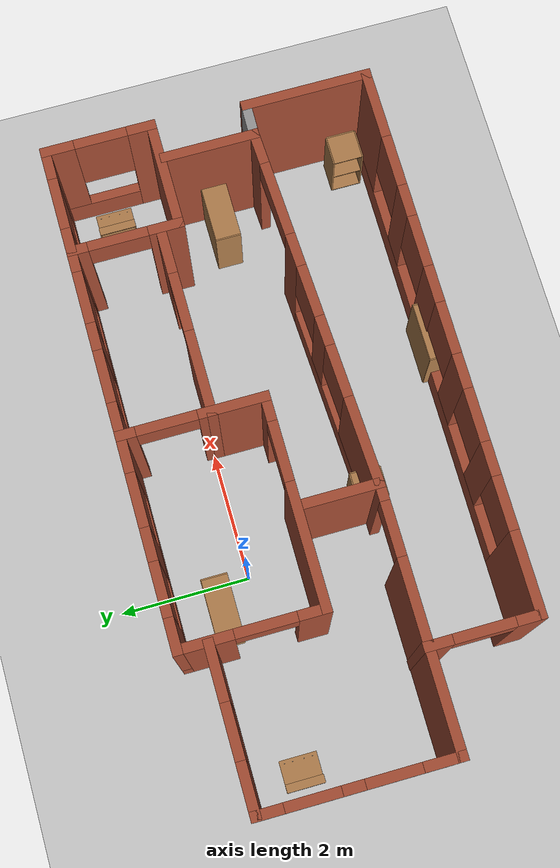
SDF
<sdf version="1.6">
 <world name="default">
  <light name="sun" type="directional">
   <pose>0 0 15 0 -0 0</pose>
   <diffuse>0.8 0.8 0.8 1</diffuse>
   <specular>0.2 0.2 0.2 1</specular>
   <attenuation>
    <range>1000</range>
    <constant>0.9</constant>
    <linear>0.01</linear>
    <quadratic>0.001</quadratic>
   </attenuation>
   <direction>-0.5 0.1 -0.9</direction>
  </light>
  <model name="ground_plane">
   <static>1</static>
   <link name="link">
    <collision name="collision">
     <geometry><plane><normal>0 0 1</normal><size>100 100</size></plane></geometry>
     <surface><friction><ode><mu>100</mu><mu2>50</mu2></ode></friction></surface>
    </collision>
    <visual name="visual">
     <transparency>1</transparency>
     <cast_shadows>0</cast_shadows>
     <geometry><plane><normal>0 0 1</normal><size>100 100</size></plane></geometry>
     <material>
      <script><uri>file://media/materials/scripts/gazebo.material</uri><name>Gazebo/Grey</name></script>
     </material>
    </visual>
   </link>
  </model>
  <gravity>0 0 -9.8</gravity>
  <magnetic_field>6e-06 2.3e-05 -4.2e-05</magnetic_field>
  <atmosphere type="adiabatic"/>
  <physics name="default_physics" default="0" type="ode">
   <max_step_size>0.001</max_step_size>
   <real_time_factor>1</real_time_factor>
   <real_time_update_rate>1000</real_time_update_rate>
  </physics>
  <scene><ambient>0.4 0.4 0.4 1</ambient><background>0.7 0.7 0.7 1</background><shadows>1</shadows></scene>
  <spherical_coordinates>
   <surface_model>EARTH_WGS84</surface_model>
   <latitude_deg>0</latitude_deg>
   <longitude_deg>0</longitude_deg>
   <elevation>0</elevation>
   <heading_deg>0</heading_deg>
  </spherical_coordinates>
  <model name="new_building">
   <pose>1.52799 -1.2 0 0 -0 0</pose>
   <link name="Wall_46">
    <pose>-1.035 2.44 0 0 -0 3.14159</pose>
    <visual name="Wall_46_Visual_0">
     <pose>-1.3125 0 1.25 0 -0 0</pose>
     <geometry><box><size>0.625 0.15 2.5</size></box></geometry>
     <material>
      <script><uri>file://media/materials/scripts/gazebo.material</uri><name>Gazebo/Bricks</name></script>
      <ambient>1 1 1 1</ambient>
     </material>
     <meta><layer>0</layer></meta>
    </visual>
    <collision name="Wall_46_Collision_0">
     <geometry><box><size>0.625 0.15 2.5</size></box></geometry>
     <pose>-1.3125 0 1.25 0 -0 0</pose>
    </collision>
    <visual name="Wall_46_Visual_1">
     <pose>0.3125 0 0.25 0 -0 0</pose>
     <geometry><box><size>2.625 0.15 0.5</size></box></geometry>
     <material>
      <script><uri>file://media/materials/scripts/gazebo.material</uri><name>Gazebo/Bricks</name></script>
      <ambient>1 1 1 1</ambient>
     </material>
     <meta><layer>0</layer></meta>
    </visual>
    <collision name="Wall_46_Collision_1">
     <geometry><box><size>2.625 0.15 0.5</size></box></geometry>
     <pose>0.3125 0 0.25 0 -0 0</pose>
    </collision>
    <visual name="Wall_46_Visual_2">
     <pose>0.045 0 1.5 0 -0 0</pose>
     <geometry><box><size>0.49 0.15 2</size></box></geometry>
     <material>
      <script><uri>file://media/materials/scripts/gazebo.material</uri><name>Gazebo/Bricks</name></script>
      <ambient>1 1 1 1</ambient>
     </material>
     <meta><layer>0</layer></meta>
    </visual>
    <collision name="Wall_46_Collision_2">
     <geometry><box><size>0.49 0.15 2</size></box></geometry>
     <pose>0.045 0 1.5 0 -0 0</pose>
    </collision>
    <visual name="Wall_46_Visual_3">
     <pose>1.3575 0 1.5 0 -0 0</pose>
     <geometry><box><size>0.535 0.15 2</size></box></geometry>
     <material>
      <script><uri>file://media/materials/scripts/gazebo.material</uri><name>Gazebo/Bricks</name></script>
      <ambient>1 1 1 1</ambient>
     </material>
     <meta><layer>0</layer></meta>
    </visual>
    <collision name="Wall_46_Collision_3">
     <geometry><box><size>0.535 0.15 2</size></box></geometry>
     <pose>1.3575 0 1.5 0 -0 0</pose>
    </collision>
    <visual name="Wall_46_Visual_4">
     <pose>-0.6 0 1.9 0 -0 0</pose>
     <geometry><box><size>0.8 0.15 1.2</size></box></geometry>
     <material>
      <script><uri>file://media/materials/scripts/gazebo.material</uri><name>Gazebo/Bricks</name></script>
      <ambient>1 1 1 1</ambient>
     </material>
     <meta><layer>0</layer></meta>
    </visual>
    <collision name="Wall_46_Collision_4">
     <geometry><box><size>0.8 0.15 1.2</size></box></geometry>
     <pose>-0.6 0 1.9 0 -0 0</pose>
    </collision>
    <visual name="Wall_46_Visual_5">
     <pose>0.69 0 1.9 0 -0 0</pose>
     <geometry><box><size>0.8 0.15 1.2</size></box></geometry>
     <material>
      <script><uri>file://media/materials/scripts/gazebo.material</uri><name>Gazebo/Bricks</name></script>
      <ambient>1 1 1 1</ambient>
     </material>
     <meta><layer>0</layer></meta>
    </visual>
    <collision name="Wall_46_Collision_5">
     <geometry><box><size>0.8 0.15 1.2</size></box></geometry>
     <pose>0.69 0 1.9 0 -0 0</pose>
    </collision>
   </link>
   <link name="Wall_47">
    <pose>-2.585 1.39 0 0 0 -1.5708</pose>
    <visual name="Wall_47_Visual_0">
     <pose>-0.6875 0 1.25 0 -0 0</pose>
     <geometry><box><size>0.875 0.15 2.5</size></box></geometry>
     <material>
      <script><uri>file://media/materials/scripts/gazebo.material</uri><name>Gazebo/Bricks</name></script>
      <ambient>1 1 1 1</ambient>
     </material>
     <meta><layer>0</layer></meta>
    </visual>
    <collision name="Wall_47_Collision_0">
     <geometry><box><size>0.875 0.15 2.5</size></box></geometry>
     <pose>-0.6875 0 1.25 0 -0 0</pose>
    </collision>
    <visual name="Wall_47_Visual_1">
     <pose>0.8875 0 1.25 0 -0 0</pose>
     <geometry><box><size>0.475 0.15 2.5</size></box></geometry>
     <material>
      <script><uri>file://media/materials/scripts/gazebo.material</uri><name>Gazebo/Bricks</name></script>
      <ambient>1 1 1 1</ambient>
     </material>
     <meta><layer>0</layer></meta>
    </visual>
    <collision name="Wall_47_Collision_1">
     <geometry><box><size>0.475 0.15 2.5</size></box></geometry>
     <pose>0.8875 0 1.25 0 -0 0</pose>
    </collision>
    <visual name="Wall_47_Visual_2">
     <pose>0.2 0 2.25 0 -0 0</pose>
     <geometry><box><size>0.9 0.15 0.5</size></box></geometry>
     <material>
      <script><uri>file://media/materials/scripts/gazebo.material</uri><name>Gazebo/Bricks</name></script>
      <ambient>1 1 1 1</ambient>
     </material>
     <meta><layer>0</layer></meta>
    </visual>
    <collision name="Wall_47_Collision_2">
     <geometry><box><size>0.9 0.15 0.5</size></box></geometry>
     <pose>0.2 0 2.25 0 -0 0</pose>
    </collision>
   </link>
   <link name="Wall_51">
    <pose>-1.035 0.34 0 0 -0 0</pose>
    <visual name="Wall_51_Visual_0">
     <pose>-0.6725 0 1.25 0 -0 0</pose>
     <geometry><box><size>1.905 0.15 2.5</size></box></geometry>
     <material>
      <script><uri>file://media/materials/scripts/gazebo.material</uri><name>Gazebo/Bricks</name></script>
      <ambient>1 1 1 1</ambient>
     </material>
     <meta><layer>0</layer></meta>
    </visual>
    <collision name="Wall_51_Collision_0">
     <geometry><box><size>1.905 0.15 2.5</size></box></geometry>
     <pose>-0.6725 0 1.25 0 -0 0</pose>
    </collision>
    <visual name="Wall_51_Visual_1">
     <pose>1.4025 0 1.25 0 -0 0</pose>
     <geometry><box><size>0.445 0.15 2.5</size></box></geometry>
     <material>
      <script><uri>file://media/materials/scripts/gazebo.material</uri><name>Gazebo/Bricks</name></script>
      <ambient>1 1 1 1</ambient>
     </material>
     <meta><layer>0</layer></meta>
    </visual>
    <collision name="Wall_51_Collision_1">
     <geometry><box><size>0.445 0.15 2.5</size></box></geometry>
     <pose>1.4025 0 1.25 0 -0 0</pose>
    </collision>
    <visual name="Wall_51_Visual_2">
     <pose>0.73 0 2.25 0 -0 0</pose>
     <geometry><box><size>0.9 0.15 0.5</size></box></geometry>
     <material>
      <script><uri>file://media/materials/scripts/gazebo.material</uri><name>Gazebo/Bricks</name></script>
      <ambient>1 1 1 1</ambient>
     </material>
     <meta><layer>0</layer></meta>
    </visual>
    <collision name="Wall_51_Collision_2">
     <geometry><box><size>0.9 0.15 0.5</size></box></geometry>
     <pose>0.73 0 2.25 0 -0 0</pose>
    </collision>
   </link>
   <link name="Wall_52">
    <pose>0.515 1.39 0 0 -0 1.5708</pose>
    <visual name="Wall_52_Visual_0">
     <pose>-0.5975 0 1.25 0 -0 0</pose>
     <geometry><box><size>1.055 0.15 2.5</size></box></geometry>
     <material>
      <script><uri>file://media/materials/scripts/gazebo.material</uri><name>Gazebo/Bricks</name></script>
      <ambient>1 1 1 1</ambient>
     </material>
     <meta><layer>0</layer></meta>
    </visual>
    <collision name="Wall_52_Collision_0">
     <geometry><box><size>1.055 0.15 2.5</size></box></geometry>
     <pose>-0.5975 0 1.25 0 -0 0</pose>
    </collision>
    <visual name="Wall_52_Visual_1">
     <pose>0.9775 0 1.25 0 -0 0</pose>
     <geometry><box><size>0.295 0.15 2.5</size></box></geometry>
     <material>
      <script><uri>file://media/materials/scripts/gazebo.material</uri><name>Gazebo/Bricks</name></script>
      <ambient>1 1 1 1</ambient>
     </material>
     <meta><layer>0</layer></meta>
    </visual>
    <collision name="Wall_52_Collision_1">
     <geometry><box><size>0.295 0.15 2.5</size></box></geometry>
     <pose>0.9775 0 1.25 0 -0 0</pose>
    </collision>
    <visual name="Wall_52_Visual_2">
     <pose>0.38 0 2.25 0 -0 0</pose>
     <geometry><box><size>0.9 0.15 0.5</size></box></geometry>
     <material>
      <script><uri>file://media/materials/scripts/gazebo.material</uri><name>Gazebo/Bricks</name></script>
      <ambient>1 1 1 1</ambient>
     </material>
     <meta><layer>0</layer></meta>
    </visual>
    <collision name="Wall_52_Collision_2">
     <geometry><box><size>0.9 0.15 0.5</size></box></geometry>
     <pose>0.38 0 2.25 0 -0 0</pose>
    </collision>
   </link>
   <link name="Wall_53">
    <pose>1.94 2.44 0 0 -0 0</pose>
    <visual name="Wall_53_Visual_0">
     <pose>-1.2125 0 1.25 0 -0 0</pose>
     <geometry><box><size>0.575 0.15 2.5</size></box></geometry>
     <material>
      <script><uri>file://media/materials/scripts/gazebo.material</uri><name>Gazebo/Bricks</name></script>
      <ambient>1 1 1 1</ambient>
     </material>
     <meta><layer>0</layer></meta>
    </visual>
    <collision name="Wall_53_Collision_0">
     <geometry><box><size>0.575 0.15 2.5</size></box></geometry>
     <pose>-1.2125 0 1.25 0 -0 0</pose>
    </collision>
    <visual name="Wall_53_Visual_1">
     <pose>0.2875 0 0.25 0 -0 0</pose>
     <geometry><box><size>2.425 0.15 0.5</size></box></geometry>
     <material>
      <script><uri>file://media/materials/scripts/gazebo.material</uri><name>Gazebo/Bricks</name></script>
      <ambient>1 1 1 1</ambient>
     </material>
     <meta><layer>0</layer></meta>
    </visual>
    <collision name="Wall_53_Collision_1">
     <geometry><box><size>2.425 0.15 0.5</size></box></geometry>
     <pose>0.2875 0 0.25 0 -0 0</pose>
    </collision>
    <visual name="Wall_53_Visual_2">
     <pose>0.085 0 1.5 0 -0 0</pose>
     <geometry><box><size>0.42 0.15 2</size></box></geometry>
     <material>
      <script><uri>file://media/materials/scripts/gazebo.material</uri><name>Gazebo/Bricks</name></script>
      <ambient>1 1 1 1</ambient>
     </material>
     <meta><layer>0</layer></meta>
    </visual>
    <collision name="Wall_53_Collision_2">
     <geometry><box><size>0.42 0.15 2</size></box></geometry>
     <pose>0.085 0 1.5 0 -0 0</pose>
    </collision>
    <visual name="Wall_53_Visual_3">
     <pose>1.2975 0 1.5 0 -0 0</pose>
     <geometry><box><size>0.405 0.15 2</size></box></geometry>
     <material>
      <script><uri>file://media/materials/scripts/gazebo.material</uri><name>Gazebo/Bricks</name></script>
      <ambient>1 1 1 1</ambient>
     </material>
     <meta><layer>0</layer></meta>
    </visual>
    <collision name="Wall_53_Collision_3">
     <geometry><box><size>0.405 0.15 2</size></box></geometry>
     <pose>1.2975 0 1.5 0 -0 0</pose>
    </collision>
    <visual name="Wall_53_Visual_4">
     <pose>-0.525 0 1.9 0 -0 0</pose>
     <geometry><box><size>0.8 0.15 1.2</size></box></geometry>
     <material>
      <script><uri>file://media/materials/scripts/gazebo.material</uri><name>Gazebo/Bricks</name></script>
      <ambient>1 1 1 1</ambient>
     </material>
     <meta><layer>0</layer></meta>
    </visual>
    <collision name="Wall_53_Collision_4">
     <geometry><box><size>0.8 0.15 1.2</size></box></geometry>
     <pose>-0.525 0 1.9 0 -0 0</pose>
    </collision>
    <visual name="Wall_53_Visual_5">
     <pose>0.695 0 1.9 0 -0 0</pose>
     <geometry><box><size>0.8 0.15 1.2</size></box></geometry>
     <material>
      <script><uri>file://media/materials/scripts/gazebo.material</uri><name>Gazebo/Bricks</name></script>
      <ambient>1 1 1 1</ambient>
     </material>
     <meta><layer>0</layer></meta>
    </visual>
    <collision name="Wall_53_Collision_5">
     <geometry><box><size>0.8 0.15 1.2</size></box></geometry>
     <pose>0.695 0 1.9 0 -0 0</pose>
    </collision>
   </link>
   <link name="Wall_54">
    <pose>3.365 1.64 0 0 0 -1.5708</pose>
    <visual name="Wall_54_Visual_0">
     <pose>-0.7175 0 1.25 0 -0 0</pose>
     <geometry><box><size>0.315 0.15 2.5</size></box></geometry>
     <material>
      <script><uri>file://media/materials/scripts/gazebo.material</uri><name>Gazebo/Bricks</name></script>
      <ambient>1 1 1 1</ambient>
     </material>
     <meta><layer>0</layer></meta>
    </visual>
    <collision name="Wall_54_Collision_0">
     <geometry><box><size>0.315 0.15 2.5</size></box></geometry>
     <pose>-0.7175 0 1.25 0 -0 0</pose>
    </collision>
    <visual name="Wall_54_Visual_1">
     <pose>0.6075 0 1.25 0 -0 0</pose>
     <geometry><box><size>0.535 0.15 2.5</size></box></geometry>
     <material>
      <script><uri>file://media/materials/scripts/gazebo.material</uri><name>Gazebo/Bricks</name></script>
      <ambient>1 1 1 1</ambient>
     </material>
     <meta><layer>0</layer></meta>
    </visual>
    <collision name="Wall_54_Collision_1">
     <geometry><box><size>0.535 0.15 2.5</size></box></geometry>
     <pose>0.6075 0 1.25 0 -0 0</pose>
    </collision>
    <visual name="Wall_54_Visual_2">
     <pose>-0.11 0 2.25 0 -0 0</pose>
     <geometry><box><size>0.9 0.15 0.5</size></box></geometry>
     <material>
      <script><uri>file://media/materials/scripts/gazebo.material</uri><name>Gazebo/Bricks</name></script>
      <ambient>1 1 1 1</ambient>
     </material>
     <meta><layer>0</layer></meta>
    </visual>
    <collision name="Wall_54_Collision_2">
     <geometry><box><size>0.9 0.15 0.5</size></box></geometry>
     <pose>-0.11 0 2.25 0 -0 0</pose>
    </collision>
   </link>
   <link name="Wall_55">
    <collision name="Wall_55_Collision">
     <geometry><box><size>1.75 0.15 2.5</size></box></geometry>
     <pose>0 0 1.25 0 -0 0</pose>
    </collision>
    <visual name="Wall_55_Visual">
     <pose>0 0 1.25 0 -0 0</pose>
     <geometry><box><size>1.75 0.15 2.5</size></box></geometry>
     <material>
      <script><uri>file://media/materials/scripts/gazebo.material</uri><name>Gazebo/Bricks</name></script>
      <ambient>1 1 1 1</ambient>
     </material>
     <meta><layer>0</layer></meta>
    </visual>
    <pose>4.165 0.84 0 0 -0 0</pose>
   </link>
   <link name="Wall_56">
    <pose>4.965 1.64 0 0 -0 1.5708</pose>
    <visual name="Wall_56_Visual_0">
     <pose>-0.6525 0 1.25 0 -0 0</pose>
     <geometry><box><size>0.445 0.15 2.5</size></box></geometry>
     <material>
      <script><uri>file://media/materials/scripts/gazebo.material</uri><name>Gazebo/Bricks</name></script>
      <ambient>1 1 1 1</ambient>
     </material>
     <meta><layer>0</layer></meta>
    </visual>
    <collision name="Wall_56_Collision_0">
     <geometry><box><size>0.445 0.15 2.5</size></box></geometry>
     <pose>-0.6525 0 1.25 0 -0 0</pose>
    </collision>
    <visual name="Wall_56_Visual_1">
     <pose>0.2225 0 0.25 0 -0 0</pose>
     <geometry><box><size>1.305 0.15 0.5</size></box></geometry>
     <material>
      <script><uri>file://media/materials/scripts/gazebo.material</uri><name>Gazebo/Bricks</name></script>
      <ambient>1 1 1 1</ambient>
     </material>
     <meta><layer>0</layer></meta>
    </visual>
    <collision name="Wall_56_Collision_1">
     <geometry><box><size>1.305 0.15 0.5</size></box></geometry>
     <pose>0.2225 0 0.25 0 -0 0</pose>
    </collision>
    <visual name="Wall_56_Visual_2">
     <pose>0.6225 0 1.5 0 -0 0</pose>
     <geometry><box><size>0.505 0.15 2</size></box></geometry>
     <material>
      <script><uri>file://media/materials/scripts/gazebo.material</uri><name>Gazebo/Bricks</name></script>
      <ambient>1 1 1 1</ambient>
     </material>
     <meta><layer>0</layer></meta>
    </visual>
    <collision name="Wall_56_Collision_2">
     <geometry><box><size>0.505 0.15 2</size></box></geometry>
     <pose>0.6225 0 1.5 0 -0 0</pose>
    </collision>
    <visual name="Wall_56_Visual_3">
     <pose>-0.03 0 1.9 0 -0 0</pose>
     <geometry><box><size>0.8 0.15 1.2</size></box></geometry>
     <material>
      <script><uri>file://media/materials/scripts/gazebo.material</uri><name>Gazebo/Bricks</name></script>
      <ambient>1 1 1 1</ambient>
     </material>
     <meta><layer>0</layer></meta>
    </visual>
    <collision name="Wall_56_Collision_3">
     <geometry><box><size>0.8 0.15 1.2</size></box></geometry>
     <pose>-0.03 0 1.9 0 -0 0</pose>
    </collision>
   </link>
   <link name="Wall_57">
    <pose>4.165 2.44 0 0 0 -3.14159</pose>
    <visual name="Wall_57_Visual_0">
     <pose>-0.6175 0 1.25 0 -0 0</pose>
     <geometry><box><size>0.515 0.15 2.5</size></box></geometry>
     <material>
      <script><uri>file://media/materials/scripts/gazebo.material</uri><name>Gazebo/Bricks</name></script>
      <ambient>1 1 1 1</ambient>
     </material>
     <meta><layer>0</layer></meta>
    </visual>
    <collision name="Wall_57_Collision_0">
     <geometry><box><size>0.515 0.15 2.5</size></box></geometry>
     <pose>-0.6175 0 1.25 0 -0 0</pose>
    </collision>
    <visual name="Wall_57_Visual_1">
     <pose>0.2575 0 0.25 0 -0 0</pose>
     <geometry><box><size>1.235 0.15 0.5</size></box></geometry>
     <material>
      <script><uri>file://media/materials/scripts/gazebo.material</uri><name>Gazebo/Bricks</name></script>
      <ambient>1 1 1 1</ambient>
     </material>
     <meta><layer>0</layer></meta>
    </visual>
    <collision name="Wall_57_Collision_1">
     <geometry><box><size>1.235 0.15 0.5</size></box></geometry>
     <pose>0.2575 0 0.25 0 -0 0</pose>
    </collision>
    <visual name="Wall_57_Visual_2">
     <pose>0.6575 0 1.5 0 -0 0</pose>
     <geometry><box><size>0.435 0.15 2</size></box></geometry>
     <material>
      <script><uri>file://media/materials/scripts/gazebo.material</uri><name>Gazebo/Bricks</name></script>
      <ambient>1 1 1 1</ambient>
     </material>
     <meta><layer>0</layer></meta>
    </visual>
    <collision name="Wall_57_Collision_2">
     <geometry><box><size>0.435 0.15 2</size></box></geometry>
     <pose>0.6575 0 1.5 0 -0 0</pose>
    </collision>
    <visual name="Wall_57_Visual_3">
     <pose>0.04 0 1.9 0 -0 0</pose>
     <geometry><box><size>0.8 0.15 1.2</size></box></geometry>
     <material>
      <script><uri>file://media/materials/scripts/gazebo.material</uri><name>Gazebo/Bricks</name></script>
      <ambient>1 1 1 1</ambient>
     </material>
     <meta><layer>0</layer></meta>
    </visual>
    <collision name="Wall_57_Collision_3">
     <geometry><box><size>0.8 0.15 1.2</size></box></geometry>
     <pose>0.04 0 1.9 0 -0 0</pose>
    </collision>
   </link>
   <link name="Wall_59">
    <pose>1.94 1.12 0 0 -0 0</pose>
    <visual name="Wall_59_Visual_0">
     <pose>-0.8475 0 1.25 0 -0 0</pose>
     <geometry><box><size>1.305 0.15 2.5</size></box></geometry>
     <material>
      <script><uri>file://media/materials/scripts/gazebo.material</uri><name>Gazebo/Bricks</name></script>
      <ambient>1 1 1 1</ambient>
     </material>
     <meta><layer>0</layer></meta>
    </visual>
    <collision name="Wall_59_Collision_0">
     <geometry><box><size>1.305 0.15 2.5</size></box></geometry>
     <pose>-0.8475 0 1.25 0 -0 0</pose>
    </collision>
    <visual name="Wall_59_Visual_1">
     <pose>1.1025 0 1.25 0 -0 0</pose>
     <geometry><box><size>0.795 0.15 2.5</size></box></geometry>
     <material>
      <script><uri>file://media/materials/scripts/gazebo.material</uri><name>Gazebo/Bricks</name></script>
      <ambient>1 1 1 1</ambient>
     </material>
     <meta><layer>0</layer></meta>
    </visual>
    <collision name="Wall_59_Collision_1">
     <geometry><box><size>0.795 0.15 2.5</size></box></geometry>
     <pose>1.1025 0 1.25 0 -0 0</pose>
    </collision>
    <visual name="Wall_59_Visual_2">
     <pose>0.255 0 2.25 0 -0 0</pose>
     <geometry><box><size>0.9 0.15 0.5</size></box></geometry>
     <material>
      <script><uri>file://media/materials/scripts/gazebo.material</uri><name>Gazebo/Bricks</name></script>
      <ambient>1 1 1 1</ambient>
     </material>
     <meta><layer>0</layer></meta>
    </visual>
    <collision name="Wall_59_Collision_2">
     <geometry><box><size>0.9 0.15 0.5</size></box></geometry>
     <pose>0.255 0 2.25 0 -0 0</pose>
    </collision>
   </link>
   <link name="Wall_61">
    <pose>-3.79 2 0 0 -0 3.14159</pose>
    <visual name="Wall_61_Visual_0">
     <pose>-0.8075 0 1.25 0 -0 0</pose>
     <geometry><box><size>0.885 0.15 2.5</size></box></geometry>
     <material>
      <script><uri>file://media/materials/scripts/gazebo.material</uri><name>Gazebo/Bricks</name></script>
      <ambient>1 1 1 1</ambient>
     </material>
     <meta><layer>0</layer></meta>
    </visual>
    <collision name="Wall_61_Collision_0">
     <geometry><box><size>0.885 0.15 2.5</size></box></geometry>
     <pose>-0.8075 0 1.25 0 -0 0</pose>
    </collision>
    <visual name="Wall_61_Visual_1">
     <pose>0.4425 0 0.25 0 -0 0</pose>
     <geometry><box><size>1.615 0.15 0.5</size></box></geometry>
     <material>
      <script><uri>file://media/materials/scripts/gazebo.material</uri><name>Gazebo/Bricks</name></script>
      <ambient>1 1 1 1</ambient>
     </material>
     <meta><layer>0</layer></meta>
    </visual>
    <collision name="Wall_61_Collision_1">
     <geometry><box><size>1.615 0.15 0.5</size></box></geometry>
     <pose>0.4425 0 0.25 0 -0 0</pose>
    </collision>
    <visual name="Wall_61_Visual_2">
     <pose>0.8425 0 1.5 0 -0 0</pose>
     <geometry><box><size>0.815 0.15 2</size></box></geometry>
     <material>
      <script><uri>file://media/materials/scripts/gazebo.material</uri><name>Gazebo/Bricks</name></script>
      <ambient>1 1 1 1</ambient>
     </material>
     <meta><layer>0</layer></meta>
    </visual>
    <collision name="Wall_61_Collision_2">
     <geometry><box><size>0.815 0.15 2</size></box></geometry>
     <pose>0.8425 0 1.5 0 -0 0</pose>
    </collision>
    <visual name="Wall_61_Visual_3">
     <pose>0.035 0 1.9 0 -0 0</pose>
     <geometry><box><size>0.8 0.15 1.2</size></box></geometry>
     <material>
      <script><uri>file://media/materials/scripts/gazebo.material</uri><name>Gazebo/Bricks</name></script>
      <ambient>1 1 1 1</ambient>
     </material>
     <meta><layer>0</layer></meta>
    </visual>
    <collision name="Wall_61_Collision_3">
     <geometry><box><size>0.8 0.15 1.2</size></box></geometry>
     <pose>0.035 0 1.9 0 -0 0</pose>
    </collision>
   </link>
   <link name="Wall_62">
    <pose>-4.965 0.575001 0 0 0 -1.5708</pose>
    <visual name="Wall_62_Visual_0">
     <pose>-1.2675 0 1.25 0 -0 0</pose>
     <geometry><box><size>0.465 0.15 2.5</size></box></geometry>
     <material>
      <script><uri>file://media/materials/scripts/gazebo.material</uri><name>Gazebo/Bricks</name></script>
      <ambient>1 1 1 1</ambient>
     </material>
     <meta><layer>0</layer></meta>
    </visual>
    <collision name="Wall_62_Collision_0">
     <geometry><box><size>0.465 0.15 2.5</size></box></geometry>
     <pose>-1.2675 0 1.25 0 -0 0</pose>
    </collision>
    <visual name="Wall_62_Visual_1">
     <pose>0.2325 0 0.25 0 -0 0</pose>
     <geometry><box><size>2.535 0.15 0.5</size></box></geometry>
     <material>
      <script><uri>file://media/materials/scripts/gazebo.material</uri><name>Gazebo/Bricks</name></script>
      <ambient>1 1 1 1</ambient>
     </material>
     <meta><layer>0</layer></meta>
    </visual>
    <collision name="Wall_62_Collision_1">
     <geometry><box><size>2.535 0.15 0.5</size></box></geometry>
     <pose>0.2325 0 0.25 0 -0 0</pose>
    </collision>
    <visual name="Wall_62_Visual_2">
     <pose>-0.075 0 1.5 0 -0 0</pose>
     <geometry><box><size>0.32 0.15 2</size></box></geometry>
     <material>
      <script><uri>file://media/materials/scripts/gazebo.material</uri><name>Gazebo/Bricks</name></script>
      <ambient>1 1 1 1</ambient>
     </material>
     <meta><layer>0</layer></meta>
    </visual>
    <collision name="Wall_62_Collision_2">
     <geometry><box><size>0.32 0.15 2</size></box></geometry>
     <pose>-0.075 0 1.5 0 -0 0</pose>
    </collision>
    <visual name="Wall_62_Visual_3">
     <pose>1.1925 0 1.5 0 -0 0</pose>
     <geometry><box><size>0.615 0.15 2</size></box></geometry>
     <material>
      <script><uri>file://media/materials/scripts/gazebo.material</uri><name>Gazebo/Bricks</name></script>
      <ambient>1 1 1 1</ambient>
     </material>
     <meta><layer>0</layer></meta>
    </visual>
    <collision name="Wall_62_Collision_3">
     <geometry><box><size>0.615 0.15 2</size></box></geometry>
     <pose>1.1925 0 1.5 0 -0 0</pose>
    </collision>
    <visual name="Wall_62_Visual_4">
     <pose>-0.635 0 1.9 0 -0 0</pose>
     <geometry><box><size>0.8 0.15 1.2</size></box></geometry>
     <material>
      <script><uri>file://media/materials/scripts/gazebo.material</uri><name>Gazebo/Bricks</name></script>
      <ambient>1 1 1 1</ambient>
     </material>
     <meta><layer>0</layer></meta>
    </visual>
    <collision name="Wall_62_Collision_4">
     <geometry><box><size>0.8 0.15 1.2</size></box></geometry>
     <pose>-0.635 0 1.9 0 -0 0</pose>
    </collision>
    <visual name="Wall_62_Visual_5">
     <pose>0.485 0 1.9 0 -0 0</pose>
     <geometry><box><size>0.8 0.15 1.2</size></box></geometry>
     <material>
      <script><uri>file://media/materials/scripts/gazebo.material</uri><name>Gazebo/Bricks</name></script>
      <ambient>1 1 1 1</ambient>
     </material>
     <meta><layer>0</layer></meta>
    </visual>
    <collision name="Wall_62_Collision_5">
     <geometry><box><size>0.8 0.15 1.2</size></box></geometry>
     <pose>0.485 0 1.9 0 -0 0</pose>
    </collision>
   </link>
   <link name="Wall_63">
    <pose>-3.04 -0.85 0 0 -0 0</pose>
    <visual name="Wall_63_Visual_0">
     <pose>-0.5725 0 1.25 0 -0 0</pose>
     <geometry><box><size>2.855 0.15 2.5</size></box></geometry>
     <material>
      <script><uri>file://media/materials/scripts/gazebo.material</uri><name>Gazebo/Bricks</name></script>
      <ambient>1 1 1 1</ambient>
     </material>
     <meta><layer>0</layer></meta>
    </visual>
    <collision name="Wall_63_Collision_0">
     <geometry><box><size>2.855 0.15 2.5</size></box></geometry>
     <pose>-0.5725 0 1.25 0 -0 0</pose>
    </collision>
    <visual name="Wall_63_Visual_1">
     <pose>1.8325 0 1.25 0 -0 0</pose>
     <geometry><box><size>0.335 0.15 2.5</size></box></geometry>
     <material>
      <script><uri>file://media/materials/scripts/gazebo.material</uri><name>Gazebo/Bricks</name></script>
      <ambient>1 1 1 1</ambient>
     </material>
     <meta><layer>0</layer></meta>
    </visual>
    <collision name="Wall_63_Collision_1">
     <geometry><box><size>0.335 0.15 2.5</size></box></geometry>
     <pose>1.8325 0 1.25 0 -0 0</pose>
    </collision>
    <visual name="Wall_63_Visual_2">
     <pose>1.26 0 2.25 0 -0 0</pose>
     <geometry><box><size>0.81 0.15 0.5</size></box></geometry>
     <material>
      <script><uri>file://media/materials/scripts/gazebo.material</uri><name>Gazebo/Bricks</name></script>
      <ambient>1 1 1 1</ambient>
     </material>
     <meta><layer>0</layer></meta>
    </visual>
    <collision name="Wall_63_Collision_2">
     <geometry><box><size>0.81 0.15 0.5</size></box></geometry>
     <pose>1.26 0 2.25 0 -0 0</pose>
    </collision>
   </link>
   <link name="Wall_64">
    <collision name="Wall_64_Collision">
     <geometry><box><size>1.25 0.15 2.5</size></box></geometry>
     <pose>0 0 1.25 0 -0 0</pose>
    </collision>
    <visual name="Wall_64_Visual">
     <pose>0 0 1.25 0 -0 0</pose>
     <geometry><box><size>1.25 0.15 2.5</size></box></geometry>
     <material>
      <script><uri>file://media/materials/scripts/gazebo.material</uri><name>Gazebo/Bricks</name></script>
      <ambient>1 1 1 1</ambient>
     </material>
     <meta><layer>0</layer></meta>
    </visual>
    <pose>-1.115 -0.299999 0 0 -0 1.5708</pose>
   </link>
   <link name="Wall_66">
    <collision name="Wall_66_Collision">
     <geometry><box><size>1.5 0.15 2.5</size></box></geometry>
     <pose>0 0 1.25 0 -0 0</pose>
    </collision>
    <visual name="Wall_66_Visual">
     <pose>0 0 1.25 0 -0 0</pose>
     <geometry><box><size>1.5 0.15 2.5</size></box></geometry>
     <material>
      <script><uri>file://media/materials/scripts/gazebo.material</uri><name>Gazebo/Bricks</name></script>
      <ambient>1 1 1 1</ambient>
     </material>
     <meta><layer>0</layer></meta>
    </visual>
    <pose>4.415 0.095001 0 0 0 -1.5708</pose>
   </link>
   <link name="Wall_67">
    <pose>1.65 -0.715 0 0 0 -3.09281</pose>
    <visual name="Wall_67_Visual_0">
     <pose>-2.56239 0 1.25 0 -0 0</pose>
     <geometry><box><size>0.561814 0.15 2.5</size></box></geometry>
     <material>
      <script><uri>file://media/materials/scripts/gazebo.material</uri><name>Gazebo/Bricks</name></script>
      <ambient>1 1 1 1</ambient>
     </material>
     <meta><layer>0</layer></meta>
    </visual>
    <collision name="Wall_67_Collision_0">
     <geometry><box><size>0.561814 0.15 2.5</size></box></geometry>
     <pose>-2.56239 0 1.25 0 -0 0</pose>
    </collision>
    <visual name="Wall_67_Visual_1">
     <pose>-0.860469 0 1.25 0 -0 0</pose>
     <geometry><box><size>0.513864 0.15 2.5</size></box></geometry>
     <material>
      <script><uri>file://media/materials/scripts/gazebo.material</uri><name>Gazebo/Bricks</name></script>
      <ambient>1 1 1 1</ambient>
     </material>
     <meta><layer>0</layer></meta>
    </visual>
    <collision name="Wall_67_Collision_1">
     <geometry><box><size>0.513864 0.15 2.5</size></box></geometry>
     <pose>-0.860469 0 1.25 0 -0 0</pose>
    </collision>
    <visual name="Wall_67_Visual_2">
     <pose>1.11988 0 0.25 0 -0 0</pose>
     <geometry><box><size>3.44683 0.15 0.5</size></box></geometry>
     <material>
      <script><uri>file://media/materials/scripts/gazebo.material</uri><name>Gazebo/Bricks</name></script>
      <ambient>1 1 1 1</ambient>
     </material>
     <meta><layer>0</layer></meta>
    </visual>
    <collision name="Wall_67_Collision_2">
     <geometry><box><size>3.44683 0.15 0.5</size></box></geometry>
     <pose>1.11988 0 0.25 0 -0 0</pose>
    </collision>
    <visual name="Wall_67_Visual_3">
     <pose>0.427176 0 1.5 0 -0 0</pose>
     <geometry><box><size>0.461427 0.15 2</size></box></geometry>
     <material>
      <script><uri>file://media/materials/scripts/gazebo.material</uri><name>Gazebo/Bricks</name></script>
      <ambient>1 1 1 1</ambient>
     </material>
     <meta><layer>0</layer></meta>
    </visual>
    <collision name="Wall_67_Collision_3">
     <geometry><box><size>0.461427 0.15 2</size></box></geometry>
     <pose>0.427176 0 1.5 0 -0 0</pose>
    </collision>
    <visual name="Wall_67_Visual_4">
     <pose>2.15059 0 1.5 0 -0 0</pose>
     <geometry><box><size>1.3854 0.15 2</size></box></geometry>
     <material>
      <script><uri>file://media/materials/scripts/gazebo.material</uri><name>Gazebo/Bricks</name></script>
      <ambient>1 1 1 1</ambient>
     </material>
     <meta><layer>0</layer></meta>
    </visual>
    <collision name="Wall_67_Collision_4">
     <geometry><box><size>1.3854 0.15 2</size></box></geometry>
     <pose>2.15059 0 1.5 0 -0 0</pose>
    </collision>
    <visual name="Wall_67_Visual_5">
     <pose>-0.203537 0 1.9 0 -0 0</pose>
     <geometry><box><size>0.8 0.15 1.2</size></box></geometry>
     <material>
      <script><uri>file://media/materials/scripts/gazebo.material</uri><name>Gazebo/Bricks</name></script>
      <ambient>1 1 1 1</ambient>
     </material>
     <meta><layer>0</layer></meta>
    </visual>
    <collision name="Wall_67_Collision_5">
     <geometry><box><size>0.8 0.15 1.2</size></box></geometry>
     <pose>-0.203537 0 1.9 0 -0 0</pose>
    </collision>
    <visual name="Wall_67_Visual_6">
     <pose>1.05789 0 1.9 0 -0 0</pose>
     <geometry><box><size>0.8 0.15 1.2</size></box></geometry>
     <material>
      <script><uri>file://media/materials/scripts/gazebo.material</uri><name>Gazebo/Bricks</name></script>
      <ambient>1 1 1 1</ambient>
     </material>
     <meta><layer>0</layer></meta>
    </visual>
    <collision name="Wall_67_Collision_6">
     <geometry><box><size>0.8 0.15 1.2</size></box></geometry>
     <pose>1.05789 0 1.9 0 -0 0</pose>
    </collision>
    <visual name="Wall_67_Visual_7">
     <pose>-1.69944 0 2.25 0 -0 0</pose>
     <geometry><box><size>1.16408 0.15 0.5</size></box></geometry>
     <material>
      <script><uri>file://media/materials/scripts/gazebo.material</uri><name>Gazebo/Bricks</name></script>
      <ambient>1 1 1 1</ambient>
     </material>
     <meta><layer>0</layer></meta>
    </visual>
    <collision name="Wall_67_Collision_7">
     <geometry><box><size>1.16408 0.15 0.5</size></box></geometry>
     <pose>-1.69944 0 2.25 0 -0 0</pose>
    </collision>
   </link>
   <link name="Wall_70">
    <pose>-3.455 -1.64 0 0 0 -1.5708</pose>
    <visual name="Wall_70_Visual_0">
     <pose>-0.6625 0 1.25 0 -0 0</pose>
     <geometry><box><size>0.425 0.15 2.5</size></box></geometry>
     <material>
      <script><uri>file://media/materials/scripts/gazebo.material</uri><name>Gazebo/Bricks</name></script>
      <ambient>1 1 1 1</ambient>
     </material>
     <meta><layer>0</layer></meta>
    </visual>
    <collision name="Wall_70_Collision_0">
     <geometry><box><size>0.425 0.15 2.5</size></box></geometry>
     <pose>-0.6625 0 1.25 0 -0 0</pose>
    </collision>
    <visual name="Wall_70_Visual_1">
     <pose>0.6625 0 1.25 0 -0 0</pose>
     <geometry><box><size>0.425 0.15 2.5</size></box></geometry>
     <material>
      <script><uri>file://media/materials/scripts/gazebo.material</uri><name>Gazebo/Bricks</name></script>
      <ambient>1 1 1 1</ambient>
     </material>
     <meta><layer>0</layer></meta>
    </visual>
    <collision name="Wall_70_Collision_1">
     <geometry><box><size>0.425 0.15 2.5</size></box></geometry>
     <pose>0.6625 0 1.25 0 -0 0</pose>
    </collision>
    <visual name="Wall_70_Visual_2">
     <pose>-0 0 2.25 0 -0 0</pose>
     <geometry><box><size>0.9 0.15 0.5</size></box></geometry>
     <material>
      <script><uri>file://media/materials/scripts/gazebo.material</uri><name>Gazebo/Bricks</name></script>
      <ambient>1 1 1 1</ambient>
     </material>
     <meta><layer>0</layer></meta>
    </visual>
    <collision name="Wall_70_Collision_2">
     <geometry><box><size>0.9 0.15 0.5</size></box></geometry>
     <pose>-0 0 2.25 0 -0 0</pose>
    </collision>
   </link>
   <link name="Wall_71">
    <pose>0.72 -2.44 0 0 -0 0</pose>
    <visual name="Wall_71_Visual_0">
     <pose>-3.6125 0 1.25 0 -0 0</pose>
     <geometry><box><size>1.275 0.15 2.5</size></box></geometry>
     <material>
      <script><uri>file://media/materials/scripts/gazebo.material</uri><name>Gazebo/Bricks</name></script>
      <ambient>1 1 1 1</ambient>
     </material>
     <meta><layer>0</layer></meta>
    </visual>
    <collision name="Wall_71_Collision_0">
     <geometry><box><size>1.275 0.15 2.5</size></box></geometry>
     <pose>-3.6125 0 1.25 0 -0 0</pose>
    </collision>
    <visual name="Wall_71_Visual_1">
     <pose>0.6375 0 0.25 0 -0 0</pose>
     <geometry><box><size>7.225 0.15 0.5</size></box></geometry>
     <material>
      <script><uri>file://media/materials/scripts/gazebo.material</uri><name>Gazebo/Bricks</name></script>
      <ambient>1 1 1 1</ambient>
     </material>
     <meta><layer>0</layer></meta>
    </visual>
    <collision name="Wall_71_Collision_1">
     <geometry><box><size>7.225 0.15 0.5</size></box></geometry>
     <pose>0.6375 0 0.25 0 -0 0</pose>
    </collision>
    <visual name="Wall_71_Visual_2">
     <pose>-1.92 0 1.5 0 -0 0</pose>
     <geometry><box><size>0.51 0.15 2</size></box></geometry>
     <material>
      <script><uri>file://media/materials/scripts/gazebo.material</uri><name>Gazebo/Bricks</name></script>
      <ambient>1 1 1 1</ambient>
     </material>
     <meta><layer>0</layer></meta>
    </visual>
    <collision name="Wall_71_Collision_2">
     <geometry><box><size>0.51 0.15 2</size></box></geometry>
     <pose>-1.92 0 1.5 0 -0 0</pose>
    </collision>
    <visual name="Wall_71_Visual_3">
     <pose>-0.6 0 1.5 0 -0 0</pose>
     <geometry><box><size>0.53 0.15 2</size></box></geometry>
     <material>
      <script><uri>file://media/materials/scripts/gazebo.material</uri><name>Gazebo/Bricks</name></script>
      <ambient>1 1 1 1</ambient>
     </material>
     <meta><layer>0</layer></meta>
    </visual>
    <collision name="Wall_71_Collision_3">
     <geometry><box><size>0.53 0.15 2</size></box></geometry>
     <pose>-0.6 0 1.5 0 -0 0</pose>
    </collision>
    <visual name="Wall_71_Visual_4">
     <pose>0.75 0 1.5 0 -0 0</pose>
     <geometry><box><size>0.57 0.15 2</size></box></geometry>
     <material>
      <script><uri>file://media/materials/scripts/gazebo.material</uri><name>Gazebo/Bricks</name></script>
      <ambient>1 1 1 1</ambient>
     </material>
     <meta><layer>0</layer></meta>
    </visual>
    <collision name="Wall_71_Collision_4">
     <geometry><box><size>0.57 0.15 2</size></box></geometry>
     <pose>0.75 0 1.5 0 -0 0</pose>
    </collision>
    <visual name="Wall_71_Visual_5">
     <pose>2.085 0 1.5 0 -0 0</pose>
     <geometry><box><size>0.5 0.15 2</size></box></geometry>
     <material>
      <script><uri>file://media/materials/scripts/gazebo.material</uri><name>Gazebo/Bricks</name></script>
      <ambient>1 1 1 1</ambient>
     </material>
     <meta><layer>0</layer></meta>
    </visual>
    <collision name="Wall_71_Collision_5">
     <geometry><box><size>0.5 0.15 2</size></box></geometry>
     <pose>2.085 0 1.5 0 -0 0</pose>
    </collision>
    <visual name="Wall_71_Visual_6">
     <pose>3.6925 0 1.5 0 -0 0</pose>
     <geometry><box><size>1.115 0.15 2</size></box></geometry>
     <material>
      <script><uri>file://media/materials/scripts/gazebo.material</uri><name>Gazebo/Bricks</name></script>
      <ambient>1 1 1 1</ambient>
     </material>
     <meta><layer>0</layer></meta>
    </visual>
    <collision name="Wall_71_Collision_6">
     <geometry><box><size>1.115 0.15 2</size></box></geometry>
     <pose>3.6925 0 1.5 0 -0 0</pose>
    </collision>
    <visual name="Wall_71_Visual_7">
     <pose>-2.575 0 1.9 0 -0 0</pose>
     <geometry><box><size>0.8 0.15 1.2</size></box></geometry>
     <material>
      <script><uri>file://media/materials/scripts/gazebo.material</uri><name>Gazebo/Bricks</name></script>
      <ambient>1 1 1 1</ambient>
     </material>
     <meta><layer>0</layer></meta>
    </visual>
    <collision name="Wall_71_Collision_7">
     <geometry><box><size>0.8 0.15 1.2</size></box></geometry>
     <pose>-2.575 0 1.9 0 -0 0</pose>
    </collision>
    <visual name="Wall_71_Visual_8">
     <pose>-1.265 0 1.9 0 -0 0</pose>
     <geometry><box><size>0.8 0.15 1.2</size></box></geometry>
     <material>
      <script><uri>file://media/materials/scripts/gazebo.material</uri><name>Gazebo/Bricks</name></script>
      <ambient>1 1 1 1</ambient>
     </material>
     <meta><layer>0</layer></meta>
    </visual>
    <collision name="Wall_71_Collision_8">
     <geometry><box><size>0.8 0.15 1.2</size></box></geometry>
     <pose>-1.265 0 1.9 0 -0 0</pose>
    </collision>
    <visual name="Wall_71_Visual_9">
     <pose>0.065 0 1.9 0 -0 0</pose>
     <geometry><box><size>0.8 0.15 1.2</size></box></geometry>
     <material>
      <script><uri>file://media/materials/scripts/gazebo.material</uri><name>Gazebo/Bricks</name></script>
      <ambient>1 1 1 1</ambient>
     </material>
     <meta><layer>0</layer></meta>
    </visual>
    <collision name="Wall_71_Collision_9">
     <geometry><box><size>0.8 0.15 1.2</size></box></geometry>
     <pose>0.065 0 1.9 0 -0 0</pose>
    </collision>
    <visual name="Wall_71_Visual_10">
     <pose>1.435 0 1.9 0 -0 0</pose>
     <geometry><box><size>0.8 0.15 1.2</size></box></geometry>
     <material>
      <script><uri>file://media/materials/scripts/gazebo.material</uri><name>Gazebo/Bricks</name></script>
      <ambient>1 1 1 1</ambient>
     </material>
     <meta><layer>0</layer></meta>
    </visual>
    <collision name="Wall_71_Collision_10">
     <geometry><box><size>0.8 0.15 1.2</size></box></geometry>
     <pose>1.435 0 1.9 0 -0 0</pose>
    </collision>
    <visual name="Wall_71_Visual_11">
     <pose>2.735 0 1.9 0 -0 0</pose>
     <geometry><box><size>0.8 0.15 1.2</size></box></geometry>
     <material>
      <script><uri>file://media/materials/scripts/gazebo.material</uri><name>Gazebo/Bricks</name></script>
      <ambient>1 1 1 1</ambient>
     </material>
     <meta><layer>0</layer></meta>
    </visual>
    <collision name="Wall_71_Collision_11">
     <geometry><box><size>0.8 0.15 1.2</size></box></geometry>
     <pose>2.735 0 1.9 0 -0 0</pose>
    </collision>
   </link>
   <link name="Wall_72">
    <collision name="Wall_72_Collision">
     <geometry><box><size>2 0.15 2.5</size></box></geometry>
     <pose>0 0 1.25 0 -0 0</pose>
    </collision>
    <visual name="Wall_72_Visual">
     <pose>0 0 1.25 0 -0 0</pose>
     <geometry><box><size>2 0.15 2.5</size></box></geometry>
     <material>
      <script><uri>file://media/materials/scripts/gazebo.material</uri><name>Gazebo/Bricks</name></script>
      <ambient>1 1 1 1</ambient>
     </material>
     <meta><layer>0</layer></meta>
    </visual>
    <pose>4.895 -1.515 0 0 -0 1.5708</pose>
   </link>
   <link name="Wall_73">
    <collision name="Wall_73_Collision">
     <geometry><box><size>0.630104 0.15 2.5</size></box></geometry>
     <pose>0 0 1.25 0 -0 0</pose>
    </collision>
    <visual name="Wall_73_Visual">
     <pose>0 0 1.25 0 -0 0</pose>
     <geometry><box><size>0.630104 0.15 2.5</size></box></geometry>
     <material>
      <script><uri>file://media/materials/scripts/gazebo.material</uri><name>Gazebo/Grey</name></script>
      <ambient>1 1 1 1</ambient>
     </material>
     <meta><layer>0</layer></meta>
    </visual>
    <pose>4.655 -0.585 0 0 -0 3.12076</pose>
   </link>
   <static>1</static>
  </model>
  <model name="cabinet">
   <static>1</static>
   <link name="cabinet_bottom_plate">
    <inertial>
     <pose>0 0 -1 0 -0 0</pose>
     <inertia><ixx>2.05</ixx><ixy>0</ixy><ixz>0</ixz><iyy>2.05</iyy><iyz>0</iyz><izz>2.05</izz></inertia>
     <mass>25</mass>
    </inertial>
    <collision name="cabinet_bottom_plate_geom">
     <pose>0 0 0.01 0 -0 0</pose>
     <geometry><box><size>0.45 0.45 0.02</size></box></geometry>
    </collision>
    <visual name="cabinet_bottom_plate_geom_visual">
     <pose>0 0 0.01 0 -0 0</pose>
     <geometry><box><size>0.45 0.45 0.02</size></box></geometry>
     <material>
      <script><uri>file://media/materials/scripts/gazebo.material</uri><name>Gazebo/Wood</name></script>
     </material>
    </visual>
    <collision name="cabinet_bottom_plate_geom_cabinet_back_plate">
     <pose>0.235 0 0.51 0 -0 0</pose>
     <geometry><box><size>0.02 0.45 1.02</size></box></geometry>
    </collision>
    <visual name="cabinet_bottom_plate_geom_cabinet_back_plate_visual">
     <pose>0.235 0 0.51 0 -0 0</pose>
     <geometry><box><size>0.02 0.45 1.02</size></box></geometry>
     <material>
      <script><uri>file://media/materials/scripts/gazebo.material</uri><name>Gazebo/Wood</name></script>
     </material>
    </visual>
    <collision name="cabinet_bottom_plate_geom_cabinet_left_plate">
     <pose>0 0.235 0.51 0 -0 0</pose>
     <geometry><box><size>0.45 0.02 1.02</size></box></geometry>
    </collision>
    <visual name="cabinet_bottom_plate_geom_cabinet_left_plate_visual">
     <pose>0 0.235 0.51 0 -0 0</pose>
     <geometry><box><size>0.45 0.02 1.02</size></box></geometry>
     <material>
      <script><uri>file://media/materials/scripts/gazebo.material</uri><name>Gazebo/Wood</name></script>
     </material>
    </visual>
    <collision name="cabinet_bottom_plate_geom_cabinet_middle_plate">
     <pose>0 0 0.51 0 -0 0</pose>
     <geometry><box><size>0.45 0.45 0.02</size></box></geometry>
    </collision>
    <visual name="cabinet_bottom_plate_geom_cabinet_middle_plate_visual">
     <pose>0 0 0.51 0 -0 0</pose>
     <geometry><box><size>0.45 0.45 0.02</size></box></geometry>
     <material>
      <script><uri>file://media/materials/scripts/gazebo.material</uri><name>Gazebo/Wood</name></script>
     </material>
    </visual>
    <collision name="cabinet_bottom_plate_geom_cabinet_right_plate">
     <pose>0 -0.235 0.51 0 -0 0</pose>
     <geometry><box><size>0.45 0.02 1.02</size></box></geometry>
    </collision>
    <visual name="cabinet_bottom_plate_geom_cabinet_right_plate_visual">
     <pose>0 -0.235 0.51 0 -0 0</pose>
     <geometry><box><size>0.45 0.02 1.02</size></box></geometry>
     <material>
      <script><uri>file://media/materials/scripts/gazebo.material</uri><name>Gazebo/Wood</name></script>
     </material>
    </visual>
    <collision name="cabinet_bottom_plate_geom_cabinet_top_plate">
     <pose>0 0 1.01 0 -0 0</pose>
     <geometry><box><size>0.45 0.45 0.02</size></box></geometry>
    </collision>
    <visual name="cabinet_bottom_plate_geom_cabinet_top_plate_visual">
     <pose>0 0 1.01 0 -0 0</pose>
     <geometry><box><size>0.45 0.45 0.02</size></box></geometry>
     <material>
      <script><uri>file://media/materials/scripts/gazebo.material</uri><name>Gazebo/Wood</name></script>
     </material>
    </visual>
   </link>
   <pose>6.02694 -3.24856 0 0 -0 0</pose>
  </model>
  <model name="bookshelf">
   <static>1</static>
   <link name="link">
    <inertial><mass>1</mass></inertial>
    <collision name="back">
     <pose>0 0.005 0.6 0 -0 0</pose>
     <geometry><box><size>0.9 0.01 1.2</size></box></geometry>
    </collision>
    <visual name="visual1">
     <pose>0 0.005 0.6 0 -0 0</pose>
     <geometry><box><size>0.9 0.01 1.2</size></box></geometry>
     <material>
      <script><uri>file://media/materials/scripts/gazebo.material</uri><name>Gazebo/Wood</name></script>
     </material>
    </visual>
    <collision name="left_side">
     <pose>0.45 -0.195 0.6 0 -0 0</pose>
     <geometry><box><size>0.02 0.4 1.2</size></box></geometry>
    </collision>
    <visual name="visual2">
     <pose>0.45 -0.195 0.6 0 -0 0</pose>
     <geometry><box><size>0.02 0.4 1.2</size></box></geometry>
     <material>
      <script><uri>file://media/materials/scripts/gazebo.material</uri><name>Gazebo/Wood</name></script>
     </material>
    </visual>
    <collision name="right_side">
     <pose>-0.45 -0.195 0.6 0 -0 0</pose>
     <geometry><box><size>0.02 0.4 1.2</size></box></geometry>
    </collision>
    <visual name="visual3">
     <pose>-0.45 -0.195 0.6 0 -0 0</pose>
     <geometry><box><size>0.02 0.4 1.2</size></box></geometry>
     <material>
      <script><uri>file://media/materials/scripts/gazebo.material</uri><name>Gazebo/Wood</name></script>
     </material>
    </visual>
    <collision name="bottom">
     <pose>0 -0.195 0.03 0 -0 0</pose>
     <geometry><box><size>0.88 0.4 0.06</size></box></geometry>
    </collision>
    <visual name="visual4">
     <pose>0 -0.195 0.03 0 -0 0</pose>
     <geometry><box><size>0.88 0.4 0.06</size></box></geometry>
     <material>
      <script><uri>file://media/materials/scripts/gazebo.material</uri><name>Gazebo/Wood</name></script>
     </material>
    </visual>
    <collision name="top">
     <pose>0 -0.195 1.19 0 -0 0</pose>
     <geometry><box><size>0.88 0.4 0.02</size></box></geometry>
    </collision>
    <visual name="visual5">
     <pose>0 -0.195 1.19 0 -0 0</pose>
     <geometry><box><size>0.88 0.4 0.02</size></box></geometry>
     <material>
      <script><uri>file://media/materials/scripts/gazebo.material</uri><name>Gazebo/Wood</name></script>
     </material>
    </visual>
    <collision name="low_shelf">
     <pose>0 -0.195 0.43 0 -0 0</pose>
     <geometry><box><size>0.88 0.4 0.02</size></box></geometry>
    </collision>
    <visual name="visual6">
     <pose>0 -0.195 0.43 0 -0 0</pose>
     <geometry><box><size>0.88 0.4 0.02</size></box></geometry>
     <material>
      <script><uri>file://media/materials/scripts/gazebo.material</uri><name>Gazebo/Wood</name></script>
     </material>
    </visual>
    <collision name="high_shelf">
     <pose>0 -0.195 0.8 0 -0 0</pose>
     <geometry><box><size>0.88 0.4 0.02</size></box></geometry>
    </collision>
    <visual name="visual7">
     <pose>0 -0.195 0.8 0 -0 0</pose>
     <geometry><box><size>0.88 0.4 0.02</size></box></geometry>
     <material>
      <script><uri>file://media/materials/scripts/gazebo.material</uri><name>Gazebo/Wood</name></script>
     </material>
    </visual>
   </link>
   <pose>5.44874 -0.888816 0 0 -0 0</pose>
  </model>
  <model name="bookshelf_0">
   <static>1</static>
   <link name="link">
    <inertial><mass>1</mass></inertial>
    <collision name="back">
     <pose>0 0.005 0.6 0 -0 0</pose>
     <geometry><box><size>0.9 0.01 1.2</size></box></geometry>
    </collision>
    <visual name="visual1">
     <pose>0 0.005 0.6 0 -0 0</pose>
     <geometry><box><size>0.9 0.01 1.2</size></box></geometry>
     <material>
      <script><uri>file://media/materials/scripts/gazebo.material</uri><name>Gazebo/Wood</name></script>
     </material>
    </visual>
    <collision name="left_side">
     <pose>0.45 -0.195 0.6 0 -0 0</pose>
     <geometry><box><size>0.02 0.4 1.2</size></box></geometry>
    </collision>
    <visual name="visual2">
     <pose>0.45 -0.195 0.6 0 -0 0</pose>
     <geometry><box><size>0.02 0.4 1.2</size></box></geometry>
     <material>
      <script><uri>file://media/materials/scripts/gazebo.material</uri><name>Gazebo/Wood</name></script>
     </material>
    </visual>
    <collision name="right_side">
     <pose>-0.45 -0.195 0.6 0 -0 0</pose>
     <geometry><box><size>0.02 0.4 1.2</size></box></geometry>
    </collision>
    <visual name="visual3">
     <pose>-0.45 -0.195 0.6 0 -0 0</pose>
     <geometry><box><size>0.02 0.4 1.2</size></box></geometry>
     <material>
      <script><uri>file://media/materials/scripts/gazebo.material</uri><name>Gazebo/Wood</name></script>
     </material>
    </visual>
    <collision name="bottom">
     <pose>0 -0.195 0.03 0 -0 0</pose>
     <geometry><box><size>0.88 0.4 0.06</size></box></geometry>
    </collision>
    <visual name="visual4">
     <pose>0 -0.195 0.03 0 -0 0</pose>
     <geometry><box><size>0.88 0.4 0.06</size></box></geometry>
     <material>
      <script><uri>file://media/materials/scripts/gazebo.material</uri><name>Gazebo/Wood</name></script>
     </material>
    </visual>
    <collision name="top">
     <pose>0 -0.195 1.19 0 -0 0</pose>
     <geometry><box><size>0.88 0.4 0.02</size></box></geometry>
    </collision>
    <visual name="visual5">
     <pose>0 -0.195 1.19 0 -0 0</pose>
     <geometry><box><size>0.88 0.4 0.02</size></box></geometry>
     <material>
      <script><uri>file://media/materials/scripts/gazebo.material</uri><name>Gazebo/Wood</name></script>
     </material>
    </visual>
    <collision name="low_shelf">
     <pose>0 -0.195 0.43 0 -0 0</pose>
     <geometry><box><size>0.88 0.4 0.02</size></box></geometry>
    </collision>
    <visual name="visual6">
     <pose>0 -0.195 0.43 0 -0 0</pose>
     <geometry><box><size>0.88 0.4 0.02</size></box></geometry>
     <material>
      <script><uri>file://media/materials/scripts/gazebo.material</uri><name>Gazebo/Wood</name></script>
     </material>
    </visual>
    <collision name="high_shelf">
     <pose>0 -0.195 0.8 0 -0 0</pose>
     <geometry><box><size>0.88 0.4 0.02</size></box></geometry>
    </collision>
    <visual name="visual7">
     <pose>0 -0.195 0.8 0 -0 0</pose>
     <geometry><box><size>0.88 0.4 0.02</size></box></geometry>
     <material>
      <script><uri>file://media/materials/scripts/gazebo.material</uri><name>Gazebo/Wood</name></script>
     </material>
    </visual>
   </link>
   <pose>-0.463001 0.694694 0 0 -0 0</pose>
  </model>
  <model name="wooden_case_metal_peg">
   <link name="wooden_case::base">
    <pose>0 0 0.024 0 -0 0</pose>
    <inertial>
     <pose>-0.022184 0 0.171592 0 -0 0</pose>
     <mass>3.96264</mass>
     <inertia>
      <ixx>0.213536</ixx>
      <ixy>0</ixy>
      <ixz>0.000779377</ixz>
      <iyy>0.0708943</iyy>
      <iyz>0</iyz>
      <izz>0.154604</izz>
     </inertia>
    </inertial>
    <collision name="collision_back">
     <pose>-0.053975 0 0.1778 0 -0 0</pose>
     <geometry><box><size>0.01905 0.5461 0.3175</size></box></geometry>
     <surface>
      <contact>
       <poissons_ratio>0.347</poissons_ratio>
       <elastic_modulus>8.8e+09</elastic_modulus>
       <ode><kp>100000</kp><kd>100</kd><max_vel>100</max_vel><min_depth>0.001</min_depth></ode>
      </contact>
      <friction>
       <torsional>
        <coefficient>1</coefficient>
        <use_patch_radius>0</use_patch_radius>
        <surface_radius>0.01</surface_radius>
       </torsional>
      </friction>
     </surface>
    </collision>
    <visual name="visual_back">
     <pose>-0.053975 0 0.1778 0 -0 0</pose>
     <geometry><box><size>0.01905 0.5461 0.3175</size></box></geometry>
     <material>
      <script><uri>file://media/materials/scripts/gazebo.material</uri><name>Gazebo/Wood</name></script>
     </material>
    </visual>
    <collision name="collision_bottom">
     <pose>0 0 0.009525 0 -0 0</pose>
     <geometry><box><size>0.127 0.5842 0.01905</size></box></geometry>
     <surface>
      <contact>
       <poissons_ratio>0.347</poissons_ratio>
       <elastic_modulus>8.8e+09</elastic_modulus>
       <ode><kp>100000</kp><kd>100</kd><max_vel>100</max_vel><min_depth>0.001</min_depth></ode>
      </contact>
      <friction>
       <torsional>
        <coefficient>1</coefficient>
        <use_patch_radius>0</use_patch_radius>
        <surface_radius>0.01</surface_radius>
       </torsional>
      </friction>
     </surface>
    </collision>
    <visual name="visual_bottom">
     <pose>0 0 0.009525 0 -0 0</pose>
     <geometry><box><size>0.127 0.5842 0.01905</size></box></geometry>
     <material>
      <script><uri>file://media/materials/scripts/gazebo.material</uri><name>Gazebo/Wood</name></script>
     </material>
    </visual>
    <collision name="collision_top">
     <pose>0 0 0.346075 0 -0 0</pose>
     <geometry><box><size>0.127 0.5842 0.01905</size></box></geometry>
     <surface>
      <contact>
       <poissons_ratio>0.347</poissons_ratio>
       <elastic_modulus>8.8e+09</elastic_modulus>
       <ode><kp>100000</kp><kd>100</kd><max_vel>100</max_vel><min_depth>0.001</min_depth></ode>
      </contact>
      <friction>
       <torsional>
        <coefficient>1</coefficient>
        <use_patch_radius>0</use_patch_radius>
        <surface_radius>0.01</surface_radius>
       </torsional>
      </friction>
     </surface>
    </collision>
    <visual name="visual_top">
     <pose>0 0 0.346075 0 -0 0</pose>
     <geometry><box><size>0.127 0.5842 0.01905</size></box></geometry>
     <material>
      <script><uri>file://media/materials/scripts/gazebo.material</uri><name>Gazebo/Wood</name></script>
     </material>
    </visual>
    <collision name="collision_left">
     <pose>0 -0.282575 0.1778 0 -0 0</pose>
     <geometry><box><size>0.127 0.01905 0.3175</size></box></geometry>
     <surface>
      <contact>
       <poissons_ratio>0.347</poissons_ratio>
       <elastic_modulus>8.8e+09</elastic_modulus>
       <ode><kp>100000</kp><kd>100</kd><max_vel>100</max_vel><min_depth>0.001</min_depth></ode>
      </contact>
      <friction>
       <torsional>
        <coefficient>1</coefficient>
        <use_patch_radius>0</use_patch_radius>
        <surface_radius>0.01</surface_radius>
       </torsional>
      </friction>
     </surface>
    </collision>
    <visual name="visual_left">
     <pose>0 -0.282575 0.1778 0 -0 0</pose>
     <geometry><box><size>0.127 0.01905 0.3175</size></box></geometry>
     <material>
      <script><uri>file://media/materials/scripts/gazebo.material</uri><name>Gazebo/Wood</name></script>
     </material>
    </visual>
    <collision name="collision_right">
     <pose>0 0.282575 0.1778 0 -0 0</pose>
     <geometry><box><size>0.127 0.01905 0.3175</size></box></geometry>
     <surface>
      <contact>
       <poissons_ratio>0.347</poissons_ratio>
       <elastic_modulus>8.8e+09</elastic_modulus>
       <ode><kp>100000</kp><kd>100</kd><max_vel>100</max_vel><min_depth>0.001</min_depth></ode>
      </contact>
      <friction>
       <torsional>
        <coefficient>1</coefficient>
        <use_patch_radius>0</use_patch_radius>
        <surface_radius>0.01</surface_radius>
       </torsional>
      </friction>
     </surface>
    </collision>
    <visual name="visual_right">
     <pose>0 0.282575 0.1778 0 -0 0</pose>
     <geometry><box><size>0.127 0.01905 0.3175</size></box></geometry>
     <material>
      <script><uri>file://media/materials/scripts/gazebo.material</uri><name>Gazebo/Wood</name></script>
     </material>
    </visual>
    <collision name="collision_block_left">
     <pose>0.0095 -0.2151 -0.012 0 -0 0</pose>
     <geometry><box><size>0.108 0.05 0.024</size></box></geometry>
     <surface>
      <contact>
       <poissons_ratio>0.347</poissons_ratio>
       <elastic_modulus>8.8e+09</elastic_modulus>
       <ode><kp>100000</kp><kd>100</kd><max_vel>100</max_vel><min_depth>0.001</min_depth></ode>
      </contact>
      <friction>
       <torsional>
        <coefficient>1</coefficient>
        <use_patch_radius>0</use_patch_radius>
        <surface_radius>0.01</surface_radius>
       </torsional>
      </friction>
     </surface>
    </collision>
    <visual name="visual_block_left">
     <pose>0.0095 -0.2151 -0.012 0 -0 0</pose>
     <geometry><box><size>0.108 0.05 0.024</size></box></geometry>
     <material>
      <script><uri>file://media/materials/scripts/gazebo.material</uri><name>Gazebo/Wood</name></script>
     </material>
    </visual>
    <collision name="collision_block_right">
     <pose>0.0095 0.2151 -0.012 0 -0 0</pose>
     <geometry><box><size>0.108 0.05 0.024</size></box></geometry>
     <surface>
      <contact>
       <poissons_ratio>0.347</poissons_ratio>
       <elastic_modulus>8.8e+09</elastic_modulus>
       <ode><kp>100000</kp><kd>100</kd><max_vel>100</max_vel><min_depth>0.001</min_depth></ode>
      </contact>
      <friction>
       <torsional>
        <coefficient>1</coefficient>
        <use_patch_radius>0</use_patch_radius>
        <surface_radius>0.01</surface_radius>
       </torsional>
      </friction>
     </surface>
    </collision>
    <visual name="visual_block_right">
     <pose>0.0095 0.2151 -0.012 0 -0 0</pose>
     <geometry><box><size>0.108 0.05 0.024</size></box></geometry>
     <material>
      <script><uri>file://media/materials/scripts/gazebo.material</uri><name>Gazebo/Wood</name></script>
     </material>
    </visual>
   </link>
   <link name="wooden_case::lid">
    <pose>0.243775 0 0.009525 0 -0 0</pose>
    <inertial>
     <mass>1.97874</mass>
     <inertia>
      <ixx>0.0563367</ixx>
      <ixy>0</ixy>
      <ixz>0</ixz>
      <iyy>0.020911</iyy>
      <iyz>0</iyz>
      <izz>0.0771281</izz>
     </inertia>
    </inertial>
    <collision name="collision">
     <geometry><box><size>0.3556 0.5842 0.01905</size></box></geometry>
     <surface>
      <contact>
       <poissons_ratio>0.347</poissons_ratio>
       <elastic_modulus>8.8e+09</elastic_modulus>
       <ode><kp>100000</kp><kd>100</kd><max_vel>100</max_vel><min_depth>0.001</min_depth></ode>
      </contact>
      <friction>
       <torsional>
        <coefficient>1</coefficient>
        <use_patch_radius>0</use_patch_radius>
        <surface_radius>0.01</surface_radius>
       </torsional>
      </friction>
     </surface>
    </collision>
    <visual name="visual">
     <geometry><box><size>0.3556 0.5842 0.01905</size></box></geometry>
     <material>
      <script><uri>file://media/materials/scripts/gazebo.material</uri><name>Gazebo/Wood</name></script>
     </material>
    </visual>
    <visual name="tee_nut_1">
     <pose>0.122 -0.216 0 0 -0 0</pose>
     <geometry><cylinder><radius>0.00635</radius><length>0.0192405</length></cylinder></geometry>
     <material>
      <script><uri>file://media/materials/scripts/gazebo.material</uri><name>Gazebo/Grey</name></script>
     </material>
    </visual>
    <visual name="tee_nut_2">
     <pose>0.122 -0.088 0 0 -0 0</pose>
     <geometry><cylinder><radius>0.00635</radius><length>0.0192405</length></cylinder></geometry>
     <material>
      <script><uri>file://media/materials/scripts/gazebo.material</uri><name>Gazebo/Grey</name></script>
     </material>
    </visual>
    <visual name="tee_nut_3">
     <pose>0.122 0.088 0 0 -0 0</pose>
     <geometry><cylinder><radius>0.00635</radius><length>0.0192405</length></cylinder></geometry>
     <material>
      <script><uri>file://media/materials/scripts/gazebo.material</uri><name>Gazebo/Grey</name></script>
     </material>
    </visual>
    <visual name="tee_nut_4">
     <pose>0.122 0.216 0 0 -0 0</pose>
     <geometry><cylinder><radius>0.00635</radius><length>0.0192405</length></cylinder></geometry>
     <material>
      <script><uri>file://media/materials/scripts/gazebo.material</uri><name>Gazebo/Grey</name></script>
     </material>
    </visual>
   </link>
   <joint name="wooden_case::lid_hinge" type="revolute">
    <pose>-0.1778 0 0.01905 0 -0 0</pose>
    <parent>wooden_case::base</parent>
    <child>wooden_case::lid</child>
    <axis>
     <xyz>0 1 0</xyz>
     <limit><upper>0.523599</upper><lower>-1.5708</lower></limit>
     <use_parent_model_frame>0</use_parent_model_frame>
     <dynamics><spring_reference>0</spring_reference><spring_stiffness>0</spring_stiffness></dynamics>
    </axis>
   </joint>
   <link name="peg::link">
    <pose>0.365774 0.216 0.05005 0 -0 0</pose>
    <inertial>
     <mass>0.0121</mass>
     <inertia>
      <ixx>3.90898e-06</ixx>
      <ixy>0</ixy>
      <ixz>0</ixz>
      <iyy>3.90898e-06</iyy>
      <iyz>0</iyz>
      <izz>6.58845e-08</izz>
     </inertia>
    </inertial>
    <collision name="collision">
     <geometry><cylinder><radius>0.0033</radius><length>0.062</length></cylinder></geometry>
     <surface>
      <contact>
       <poissons_ratio>0.305</poissons_ratio>
       <elastic_modulus>2e+11</elastic_modulus>
       <ode><kp>100000</kp><kd>100</kd><max_vel>100</max_vel><min_depth>0.001</min_depth></ode>
      </contact>
      <friction>
       <torsional>
        <coefficient>1</coefficient>
        <use_patch_radius>0</use_patch_radius>
        <surface_radius>0.01</surface_radius>
       </torsional>
      </friction>
     </surface>
    </collision>
    <visual name="visual">
     <geometry><cylinder><radius>0.0033</radius><length>0.062</length></cylinder></geometry>
     <material>
      <script><uri>file://media/materials/scripts/gazebo.material</uri><name>Gazebo/Grey</name></script>
     </material>
    </visual>
   </link>
   <joint name="case_peg" type="revolute">
    <child>peg::link</child>
    <parent>wooden_case::lid</parent>
    <axis>
     <xyz>0 0 1</xyz>
     <limit><upper>0</upper><lower>0</lower></limit>
     <use_parent_model_frame>0</use_parent_model_frame>
     <dynamics><spring_reference>0</spring_reference><spring_stiffness>0</spring_stiffness></dynamics>
    </axis>
   </joint>
   <pose>-3.17722 0.01014 -0.001057 0 -0.00043 -1e-06</pose>
  </model>
  <model name="cabinet_0">
   <static>1</static>
   <link name="cabinet_bottom_plate">
    <inertial>
     <pose>0 0 -1 0 -0 0</pose>
     <inertia><ixx>2.05</ixx><ixy>0</ixy><ixz>0</ixz><iyy>2.05</iyy><iyz>0</iyz><izz>2.05</izz></inertia>
     <mass>25</mass>
    </inertial>
    <collision name="cabinet_bottom_plate_geom">
     <pose>0 0 0.01 0 -0 0</pose>
     <geometry><box><size>0.45 0.45 0.02</size></box></geometry>
    </collision>
    <visual name="cabinet_bottom_plate_geom_visual">
     <pose>0 0 0.01 0 -0 0</pose>
     <geometry><box><size>0.45 0.45 0.02</size></box></geometry>
     <material>
      <script><uri>file://media/materials/scripts/gazebo.material</uri><name>Gazebo/Wood</name></script>
     </material>
    </visual>
    <collision name="cabinet_bottom_plate_geom_cabinet_back_plate">
     <pose>0.235 0 0.51 0 -0 0</pose>
     <geometry><box><size>0.02 0.45 1.02</size></box></geometry>
    </collision>
    <visual name="cabinet_bottom_plate_geom_cabinet_back_plate_visual">
     <pose>0.235 0 0.51 0 -0 0</pose>
     <geometry><box><size>0.02 0.45 1.02</size></box></geometry>
     <material>
      <script><uri>file://media/materials/scripts/gazebo.material</uri><name>Gazebo/Wood</name></script>
     </material>
    </visual>
    <collision name="cabinet_bottom_plate_geom_cabinet_left_plate">
     <pose>0 0.235 0.51 0 -0 0</pose>
     <geometry><box><size>0.45 0.02 1.02</size></box></geometry>
    </collision>
    <visual name="cabinet_bottom_plate_geom_cabinet_left_plate_visual">
     <pose>0 0.235 0.51 0 -0 0</pose>
     <geometry><box><size>0.45 0.02 1.02</size></box></geometry>
     <material>
      <script><uri>file://media/materials/scripts/gazebo.material</uri><name>Gazebo/Wood</name></script>
     </material>
    </visual>
    <collision name="cabinet_bottom_plate_geom_cabinet_middle_plate">
     <pose>0 0 0.51 0 -0 0</pose>
     <geometry><box><size>0.45 0.45 0.02</size></box></geometry>
    </collision>
    <visual name="cabinet_bottom_plate_geom_cabinet_middle_plate_visual">
     <pose>0 0 0.51 0 -0 0</pose>
     <geometry><box><size>0.45 0.45 0.02</size></box></geometry>
     <material>
      <script><uri>file://media/materials/scripts/gazebo.material</uri><name>Gazebo/Wood</name></script>
     </material>
    </visual>
    <collision name="cabinet_bottom_plate_geom_cabinet_right_plate">
     <pose>0 -0.235 0.51 0 -0 0</pose>
     <geometry><box><size>0.45 0.02 1.02</size></box></geometry>
    </collision>
    <visual name="cabinet_bottom_plate_geom_cabinet_right_plate_visual">
     <pose>0 -0.235 0.51 0 -0 0</pose>
     <geometry><box><size>0.45 0.02 1.02</size></box></geometry>
     <material>
      <script><uri>file://media/materials/scripts/gazebo.material</uri><name>Gazebo/Wood</name></script>
     </material>
    </visual>
    <collision name="cabinet_bottom_plate_geom_cabinet_top_plate">
     <pose>0 0 1.01 0 -0 0</pose>
     <geometry><box><size>0.45 0.45 0.02</size></box></geometry>
    </collision>
    <visual name="cabinet_bottom_plate_geom_cabinet_top_plate_visual">
     <pose>0 0 1.01 0 -0 0</pose>
     <geometry><box><size>0.45 0.45 0.02</size></box></geometry>
     <material>
      <script><uri>file://media/materials/scripts/gazebo.material</uri><name>Gazebo/Wood</name></script>
     </material>
    </visual>
   </link>
   <pose>0.727015 -2.07696 0 0 -0 0</pose>
  </model>
  <model name="bookshelf_1">
   <static>1</static>
   <link name="link">
    <inertial><mass>1</mass></inertial>
    <collision name="back">
     <pose>0 0.005 0.6 0 -0 0</pose>
     <geometry><box><size>0.9 0.01 1.2</size></box></geometry>
    </collision>
    <visual name="visual1">
     <pose>0 0.005 0.6 0 -0 0</pose>
     <geometry><box><size>0.9 0.01 1.2</size></box></geometry>
     <material>
      <script><uri>file://media/materials/scripts/gazebo.material</uri><name>Gazebo/Wood</name></script>
     </material>
    </visual>
    <collision name="left_side">
     <pose>0.45 -0.195 0.6 0 -0 0</pose>
     <geometry><box><size>0.02 0.4 1.2</size></box></geometry>
    </collision>
    <visual name="visual2">
     <pose>0.45 -0.195 0.6 0 -0 0</pose>
     <geometry><box><size>0.02 0.4 1.2</size></box></geometry>
     <material>
      <script><uri>file://media/materials/scripts/gazebo.material</uri><name>Gazebo/Wood</name></script>
     </material>
    </visual>
    <collision name="right_side">
     <pose>-0.45 -0.195 0.6 0 -0 0</pose>
     <geometry><box><size>0.02 0.4 1.2</size></box></geometry>
    </collision>
    <visual name="visual3">
     <pose>-0.45 -0.195 0.6 0 -0 0</pose>
     <geometry><box><size>0.02 0.4 1.2</size></box></geometry>
     <material>
      <script><uri>file://media/materials/scripts/gazebo.material</uri><name>Gazebo/Wood</name></script>
     </material>
    </visual>
    <collision name="bottom">
     <pose>0 -0.195 0.03 0 -0 0</pose>
     <geometry><box><size>0.88 0.4 0.06</size></box></geometry>
    </collision>
    <visual name="visual4">
     <pose>0 -0.195 0.03 0 -0 0</pose>
     <geometry><box><size>0.88 0.4 0.06</size></box></geometry>
     <material>
      <script><uri>file://media/materials/scripts/gazebo.material</uri><name>Gazebo/Wood</name></script>
     </material>
    </visual>
    <collision name="top">
     <pose>0 -0.195 1.19 0 -0 0</pose>
     <geometry><box><size>0.88 0.4 0.02</size></box></geometry>
    </collision>
    <visual name="visual5">
     <pose>0 -0.195 1.19 0 -0 0</pose>
     <geometry><box><size>0.88 0.4 0.02</size></box></geometry>
     <material>
      <script><uri>file://media/materials/scripts/gazebo.material</uri><name>Gazebo/Wood</name></script>
     </material>
    </visual>
    <collision name="low_shelf">
     <pose>0 -0.195 0.43 0 -0 0</pose>
     <geometry><box><size>0.88 0.4 0.02</size></box></geometry>
    </collision>
    <visual name="visual6">
     <pose>0 -0.195 0.43 0 -0 0</pose>
     <geometry><box><size>0.88 0.4 0.02</size></box></geometry>
     <material>
      <script><uri>file://media/materials/scripts/gazebo.material</uri><name>Gazebo/Wood</name></script>
     </material>
    </visual>
    <collision name="high_shelf">
     <pose>0 -0.195 0.8 0 -0 0</pose>
     <geometry><box><size>0.88 0.4 0.02</size></box></geometry>
    </collision>
    <visual name="visual7">
     <pose>0 -0.195 0.8 0 -0 0</pose>
     <geometry><box><size>0.88 0.4 0.02</size></box></geometry>
     <material>
      <script><uri>file://media/materials/scripts/gazebo.material</uri><name>Gazebo/Wood</name></script>
     </material>
    </visual>
   </link>
   <pose>2.72576 -3.48764 0 0 -0 0</pose>
  </model>
  <model name="wooden_case">
   <link name="base">
    <pose>0 0 0.024 0 -0 0</pose>
    <inertial>
     <pose>-0.022184 0 0.171592 0 -0 0</pose>
     <mass>3.96264</mass>
     <inertia>
      <ixx>0.213536</ixx>
      <ixy>0</ixy>
      <ixz>0.000779377</ixz>
      <iyy>0.0708943</iyy>
      <iyz>0</iyz>
      <izz>0.154604</izz>
     </inertia>
    </inertial>
    <collision name="collision_back">
     <pose>-0.053975 0 0.1778 0 -0 0</pose>
     <geometry><box><size>0.01905 0.5461 0.3175</size></box></geometry>
     <surface>
      <contact>
       <poissons_ratio>0.347</poissons_ratio>
       <elastic_modulus>8.8e+09</elastic_modulus>
       <ode><kp>100000</kp><kd>100</kd><max_vel>100</max_vel><min_depth>0.001</min_depth></ode>
      </contact>
      <friction>
       <torsional>
        <coefficient>1</coefficient>
        <use_patch_radius>0</use_patch_radius>
        <surface_radius>0.01</surface_radius>
       </torsional>
      </friction>
     </surface>
    </collision>
    <visual name="visual_back">
     <pose>-0.053975 0 0.1778 0 -0 0</pose>
     <geometry><box><size>0.01905 0.5461 0.3175</size></box></geometry>
     <material>
      <script><uri>file://media/materials/scripts/gazebo.material</uri><name>Gazebo/Wood</name></script>
     </material>
    </visual>
    <collision name="collision_bottom">
     <pose>0 0 0.009525 0 -0 0</pose>
     <geometry><box><size>0.127 0.5842 0.01905</size></box></geometry>
     <surface>
      <contact>
       <poissons_ratio>0.347</poissons_ratio>
       <elastic_modulus>8.8e+09</elastic_modulus>
       <ode><kp>100000</kp><kd>100</kd><max_vel>100</max_vel><min_depth>0.001</min_depth></ode>
      </contact>
      <friction>
       <torsional>
        <coefficient>1</coefficient>
        <use_patch_radius>0</use_patch_radius>
        <surface_radius>0.01</surface_radius>
       </torsional>
      </friction>
     </surface>
    </collision>
    <visual name="visual_bottom">
     <pose>0 0 0.009525 0 -0 0</pose>
     <geometry><box><size>0.127 0.5842 0.01905</size></box></geometry>
     <material>
      <script><uri>file://media/materials/scripts/gazebo.material</uri><name>Gazebo/Wood</name></script>
     </material>
    </visual>
    <collision name="collision_top">
     <pose>0 0 0.346075 0 -0 0</pose>
     <geometry><box><size>0.127 0.5842 0.01905</size></box></geometry>
     <surface>
      <contact>
       <poissons_ratio>0.347</poissons_ratio>
       <elastic_modulus>8.8e+09</elastic_modulus>
       <ode><kp>100000</kp><kd>100</kd><max_vel>100</max_vel><min_depth>0.001</min_depth></ode>
      </contact>
      <friction>
       <torsional>
        <coefficient>1</coefficient>
        <use_patch_radius>0</use_patch_radius>
        <surface_radius>0.01</surface_radius>
       </torsional>
      </friction>
     </surface>
    </collision>
    <visual name="visual_top">
     <pose>0 0 0.346075 0 -0 0</pose>
     <geometry><box><size>0.127 0.5842 0.01905</size></box></geometry>
     <material>
      <script><uri>file://media/materials/scripts/gazebo.material</uri><name>Gazebo/Wood</name></script>
     </material>
    </visual>
    <collision name="collision_left">
     <pose>0 -0.282575 0.1778 0 -0 0</pose>
     <geometry><box><size>0.127 0.01905 0.3175</size></box></geometry>
     <surface>
      <contact>
       <poissons_ratio>0.347</poissons_ratio>
       <elastic_modulus>8.8e+09</elastic_modulus>
       <ode><kp>100000</kp><kd>100</kd><max_vel>100</max_vel><min_depth>0.001</min_depth></ode>
      </contact>
      <friction>
       <torsional>
        <coefficient>1</coefficient>
        <use_patch_radius>0</use_patch_radius>
        <surface_radius>0.01</surface_radius>
       </torsional>
      </friction>
     </surface>
    </collision>
    <visual name="visual_left">
     <pose>0 -0.282575 0.1778 0 -0 0</pose>
     <geometry><box><size>0.127 0.01905 0.3175</size></box></geometry>
     <material>
      <script><uri>file://media/materials/scripts/gazebo.material</uri><name>Gazebo/Wood</name></script>
     </material>
    </visual>
    <collision name="collision_right">
     <pose>0 0.282575 0.1778 0 -0 0</pose>
     <geometry><box><size>0.127 0.01905 0.3175</size></box></geometry>
     <surface>
      <contact>
       <poissons_ratio>0.347</poissons_ratio>
       <elastic_modulus>8.8e+09</elastic_modulus>
       <ode><kp>100000</kp><kd>100</kd><max_vel>100</max_vel><min_depth>0.001</min_depth></ode>
      </contact>
      <friction>
       <torsional>
        <coefficient>1</coefficient>
        <use_patch_radius>0</use_patch_radius>
        <surface_radius>0.01</surface_radius>
       </torsional>
      </friction>
     </surface>
    </collision>
    <visual name="visual_right">
     <pose>0 0.282575 0.1778 0 -0 0</pose>
     <geometry><box><size>0.127 0.01905 0.3175</size></box></geometry>
     <material>
      <script><uri>file://media/materials/scripts/gazebo.material</uri><name>Gazebo/Wood</name></script>
     </material>
    </visual>
    <collision name="collision_block_left">
     <pose>0.0095 -0.2151 -0.012 0 -0 0</pose>
     <geometry><box><size>0.108 0.05 0.024</size></box></geometry>
     <surface>
      <contact>
       <poissons_ratio>0.347</poissons_ratio>
       <elastic_modulus>8.8e+09</elastic_modulus>
       <ode><kp>100000</kp><kd>100</kd><max_vel>100</max_vel><min_depth>0.001</min_depth></ode>
      </contact>
      <friction>
       <torsional>
        <coefficient>1</coefficient>
        <use_patch_radius>0</use_patch_radius>
        <surface_radius>0.01</surface_radius>
       </torsional>
      </friction>
     </surface>
    </collision>
    <visual name="visual_block_left">
     <pose>0.0095 -0.2151 -0.012 0 -0 0</pose>
     <geometry><box><size>0.108 0.05 0.024</size></box></geometry>
     <material>
      <script><uri>file://media/materials/scripts/gazebo.material</uri><name>Gazebo/Wood</name></script>
     </material>
    </visual>
    <collision name="collision_block_right">
     <pose>0.0095 0.2151 -0.012 0 -0 0</pose>
     <geometry><box><size>0.108 0.05 0.024</size></box></geometry>
     <surface>
      <contact>
       <poissons_ratio>0.347</poissons_ratio>
       <elastic_modulus>8.8e+09</elastic_modulus>
       <ode><kp>100000</kp><kd>100</kd><max_vel>100</max_vel><min_depth>0.001</min_depth></ode>
      </contact>
      <friction>
       <torsional>
        <coefficient>1</coefficient>
        <use_patch_radius>0</use_patch_radius>
        <surface_radius>0.01</surface_radius>
       </torsional>
      </friction>
     </surface>
    </collision>
    <visual name="visual_block_right">
     <pose>0.0095 0.2151 -0.012 0 -0 0</pose>
     <geometry><box><size>0.108 0.05 0.024</size></box></geometry>
     <material>
      <script><uri>file://media/materials/scripts/gazebo.material</uri><name>Gazebo/Wood</name></script>
     </material>
    </visual>
   </link>
   <link name="lid">
    <pose>0.243775 0 0.009525 0 -0 0</pose>
    <inertial>
     <mass>1.97874</mass>
     <inertia>
      <ixx>0.0563367</ixx>
      <ixy>0</ixy>
      <ixz>0</ixz>
      <iyy>0.020911</iyy>
      <iyz>0</iyz>
      <izz>0.0771281</izz>
     </inertia>
    </inertial>
    <collision name="collision">
     <geometry><box><size>0.3556 0.5842 0.01905</size></box></geometry>
     <surface>
      <contact>
       <poissons_ratio>0.347</poissons_ratio>
       <elastic_modulus>8.8e+09</elastic_modulus>
       <ode><kp>100000</kp><kd>100</kd><max_vel>100</max_vel><min_depth>0.001</min_depth></ode>
      </contact>
      <friction>
       <torsional>
        <coefficient>1</coefficient>
        <use_patch_radius>0</use_patch_radius>
        <surface_radius>0.01</surface_radius>
       </torsional>
      </friction>
     </surface>
    </collision>
    <visual name="visual">
     <geometry><box><size>0.3556 0.5842 0.01905</size></box></geometry>
     <material>
      <script><uri>file://media/materials/scripts/gazebo.material</uri><name>Gazebo/Wood</name></script>
     </material>
    </visual>
    <visual name="tee_nut_1">
     <pose>0.122 -0.216 0 0 -0 0</pose>
     <geometry><cylinder><radius>0.00635</radius><length>0.0192405</length></cylinder></geometry>
     <material>
      <script><uri>file://media/materials/scripts/gazebo.material</uri><name>Gazebo/Grey</name></script>
     </material>
    </visual>
    <visual name="tee_nut_2">
     <pose>0.122 -0.088 0 0 -0 0</pose>
     <geometry><cylinder><radius>0.00635</radius><length>0.0192405</length></cylinder></geometry>
     <material>
      <script><uri>file://media/materials/scripts/gazebo.material</uri><name>Gazebo/Grey</name></script>
     </material>
    </visual>
    <visual name="tee_nut_3">
     <pose>0.122 0.088 0 0 -0 0</pose>
     <geometry><cylinder><radius>0.00635</radius><length>0.0192405</length></cylinder></geometry>
     <material>
      <script><uri>file://media/materials/scripts/gazebo.material</uri><name>Gazebo/Grey</name></script>
     </material>
    </visual>
    <visual name="tee_nut_4">
     <pose>0.122 0.216 0 0 -0 0</pose>
     <geometry><cylinder><radius>0.00635</radius><length>0.0192405</length></cylinder></geometry>
     <material>
      <script><uri>file://media/materials/scripts/gazebo.material</uri><name>Gazebo/Grey</name></script>
     </material>
    </visual>
   </link>
   <joint name="lid_hinge" type="revolute">
    <pose>-0.1778 0 0.01905 0 -0 0</pose>
    <parent>base</parent>
    <child>lid</child>
    <axis>
     <xyz>0 1 0</xyz>
     <limit><upper>0.523599</upper><lower>-1.5708</lower></limit>
     <use_parent_model_frame>0</use_parent_model_frame>
     <dynamics><spring_reference>0</spring_reference><spring_stiffness>0</spring_stiffness></dynamics>
    </axis>
   </joint>
   <pose>5.96895 0.517218 -0.001057 -0 -0.000427 -1e-06</pose>
  </model>
 </world>
</sdf>
